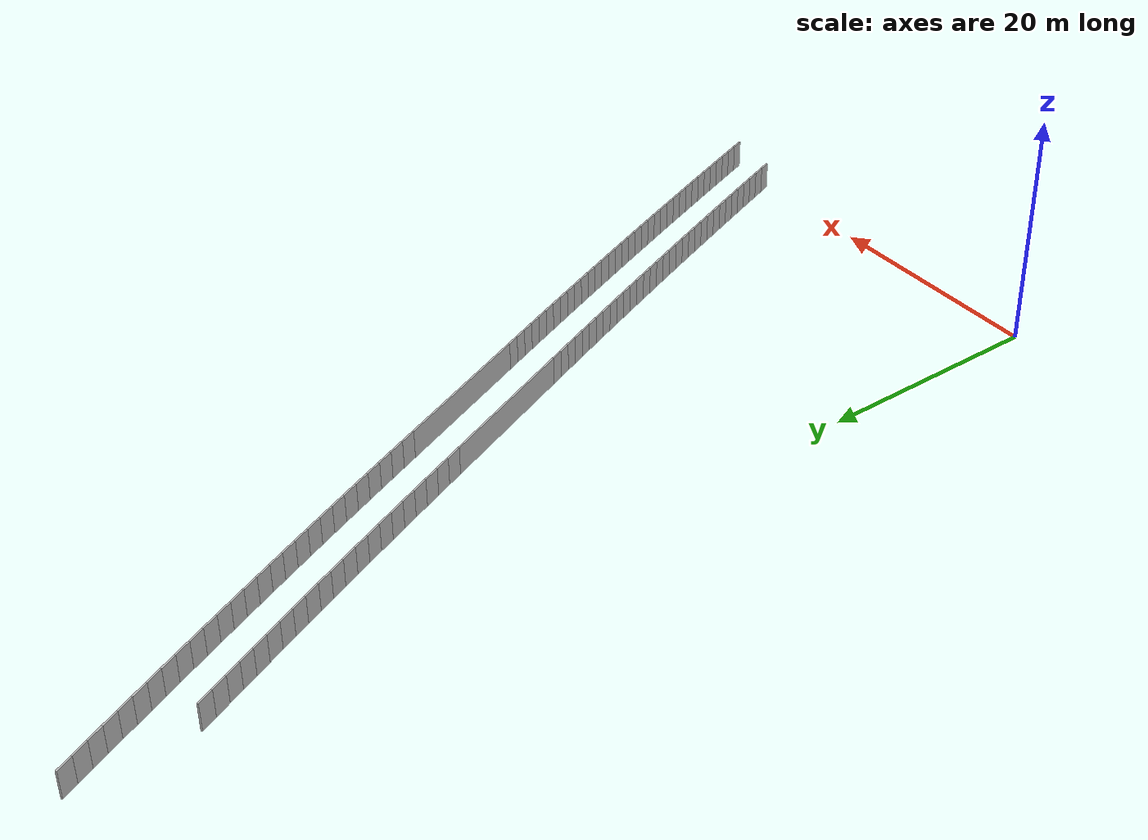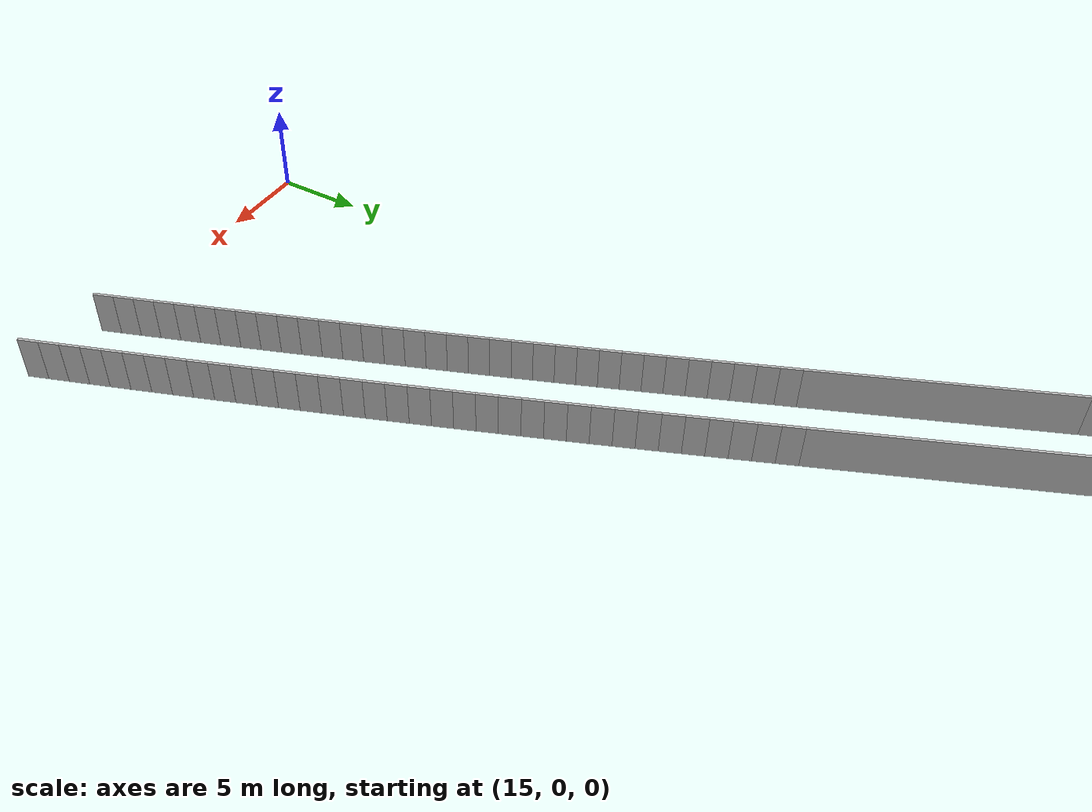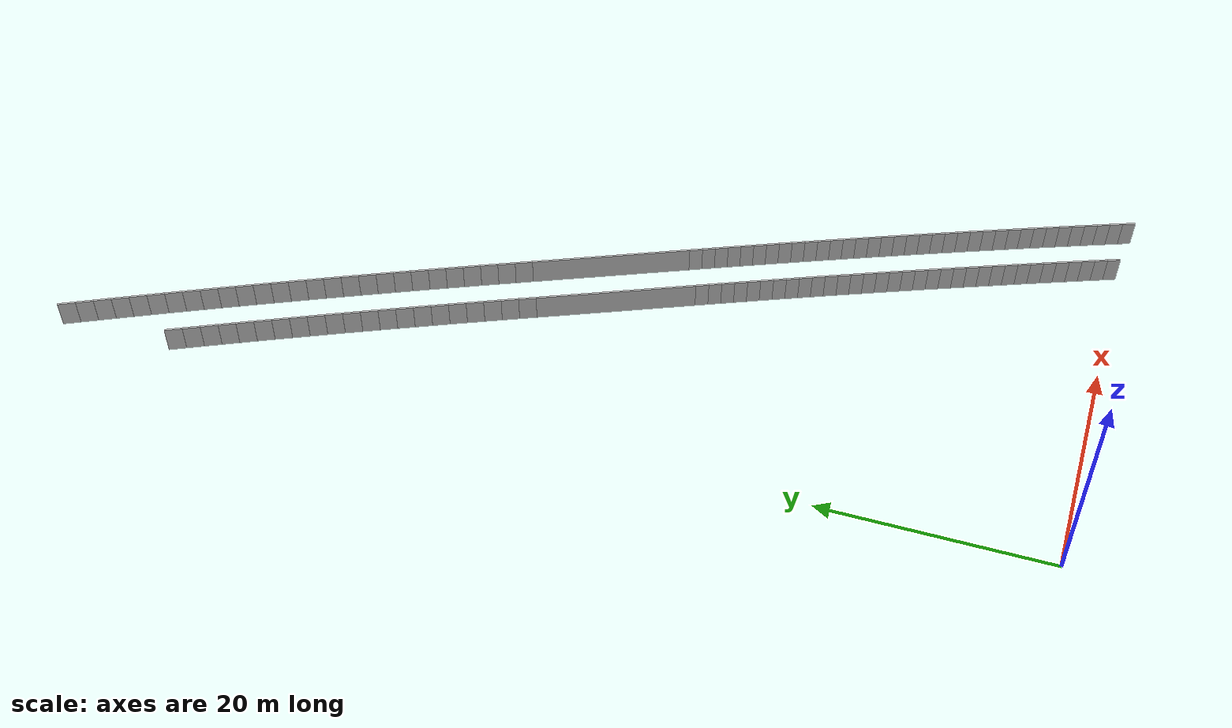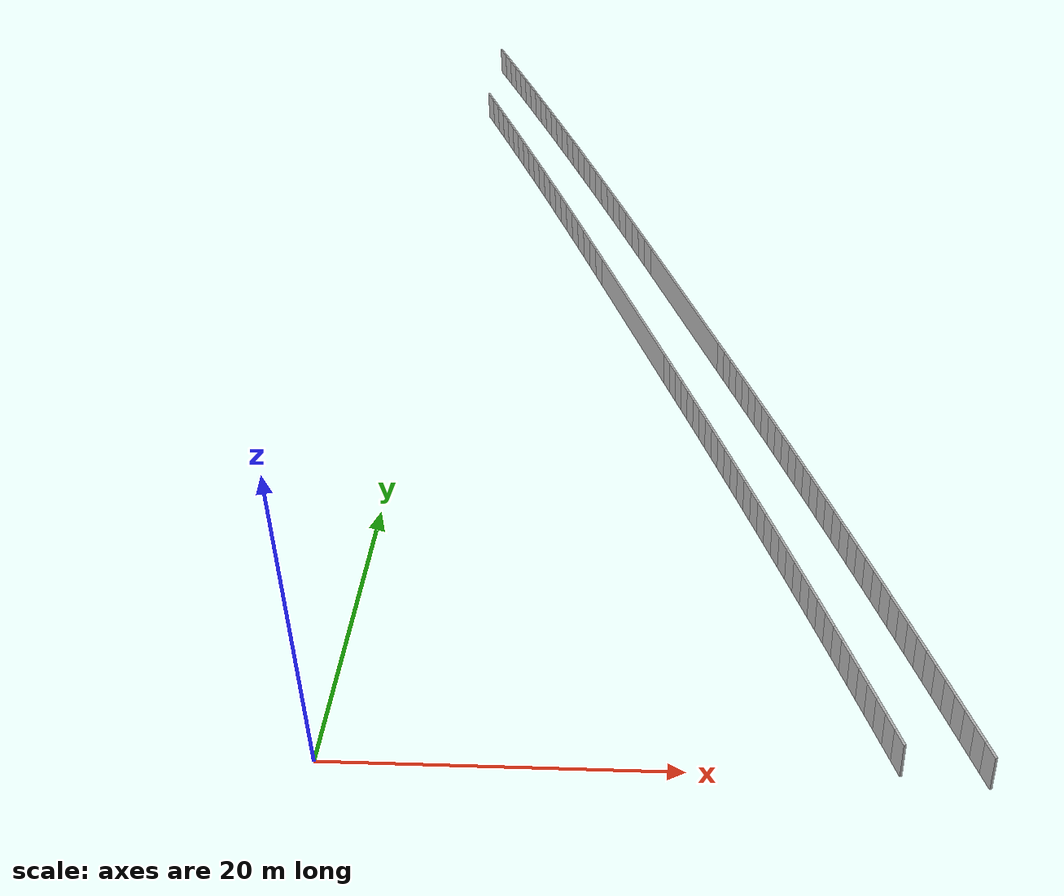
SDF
<?xml version="1.0" ?>
<sdf version="1.6">
  <model name="sps_2217">
    <pose frame="">0 0 0 0 -0 0</pose>
    <static>1</static>
    <self_collide>0</self_collide>
    <allow_auto_disable>0</allow_auto_disable>
    <link name="Wall73">
      <kinematic>0</kinematic>
      <gravity>1</gravity>
      <self_collide>0</self_collide>
      <collision name="collision">
        <geometry>
          <box>
            <size>13.7172 0.15 2.5</size>
          </box>
        </geometry>
        <pose frame="">0 0 0 0 -0 0</pose>
      </collision>
      <visual name="visual">
        <geometry>
          <box>
            <size>13.7172 0.15 2.5</size>
          </box>
        </geometry>
        <pose frame="">0 0 0 0 -0 0</pose>
        <cast_shadows>1</cast_shadows>
        <transparency>0.0</transparency>
      </visual>
      <pose frame="">19.0528 42.5171 1.25 0 0 -1.17752</pose>
    </link>
    <link name="Wall477">
      <kinematic>0</kinematic>
      <gravity>1</gravity>
      <self_collide>0</self_collide>
      <collision name="collision">
        <geometry>
          <box>
            <size>13.7271 0.15 2.5</size>
          </box>
        </geometry>
        <pose frame="">0 0 0 0 -0 0</pose>
      </collision>
      <visual name="visual">
        <geometry>
          <box>
            <size>13.7271 0.15 2.5</size>
          </box>
        </geometry>
        <pose frame="">0 0 0 0 -0 0</pose>
        <cast_shadows>1</cast_shadows>
        <transparency>0.0</transparency>
      </visual>
      <pose frame="">15.2295 40.9299 1.25 0 -0 1.96413</pose>
    </link>
    <link name="Wall3510">
      <kinematic>0</kinematic>
      <gravity>1</gravity>
      <self_collide>0</self_collide>
      <collision name="collision">
        <geometry>
          <box>
            <size>1.12133 0.15 2.5</size>
          </box>
        </geometry>
        <pose frame="">0 0 0 0 -0 0</pose>
      </collision>
      <visual name="visual">
        <geometry>
          <box>
            <size>1.12133 0.15 2.5</size>
          </box>
        </geometry>
        <pose frame="">0 0 0 0 -0 0</pose>
        <cast_shadows>1</cast_shadows>
        <transparency>0.0</transparency>
      </visual>
      <pose frame="">31.2198 0.685195 1.25 0 -0 1.92679</pose>
    </link>
    <link name="Wall3511">
      <kinematic>0</kinematic>
      <gravity>1</gravity>
      <self_collide>0</self_collide>
      <collision name="collision">
        <geometry>
          <box>
            <size>1.12134 0.15 2.5</size>
          </box>
        </geometry>
        <pose frame="">0 0 0 0 -0 0</pose>
      </collision>
      <visual name="visual">
        <geometry>
          <box>
            <size>1.12134 0.15 2.5</size>
          </box>
        </geometry>
        <pose frame="">0 0 0 0 -0 0</pose>
        <cast_shadows>1</cast_shadows>
        <transparency>0.0</transparency>
      </visual>
      <pose frame="">30.8285 1.73601 1.25 0 -0 1.92789</pose>
    </link>
    <link name="Wall3512">
      <kinematic>0</kinematic>
      <gravity>1</gravity>
      <self_collide>0</self_collide>
      <collision name="collision">
        <geometry>
          <box>
            <size>1.12145 0.15 2.5</size>
          </box>
        </geometry>
        <pose frame="">0 0 0 0 -0 0</pose>
      </collision>
      <visual name="visual">
        <geometry>
          <box>
            <size>1.12145 0.15 2.5</size>
          </box>
        </geometry>
        <pose frame="">0 0 0 0 -0 0</pose>
        <cast_shadows>1</cast_shadows>
        <transparency>0.0</transparency>
      </visual>
      <pose frame="">30.4358 2.78639 1.25 0 -0 1.92925</pose>
    </link>
    <link name="Wall3513">
      <kinematic>0</kinematic>
      <gravity>1</gravity>
      <self_collide>0</self_collide>
      <collision name="collision">
        <geometry>
          <box>
            <size>1.12134 0.15 2.5</size>
          </box>
        </geometry>
        <pose frame="">0 0 0 0 -0 0</pose>
      </collision>
      <visual name="visual">
        <geometry>
          <box>
            <size>1.12134 0.15 2.5</size>
          </box>
        </geometry>
        <pose frame="">0 0 0 0 -0 0</pose>
        <cast_shadows>1</cast_shadows>
        <transparency>0.0</transparency>
      </visual>
      <pose frame="">30.0417 3.83629 1.25 0 -0 1.93039</pose>
    </link>
    <link name="Wall3514">
      <kinematic>0</kinematic>
      <gravity>1</gravity>
      <self_collide>0</self_collide>
      <collision name="collision">
        <geometry>
          <box>
            <size>1.12144 0.15 2.5</size>
          </box>
        </geometry>
        <pose frame="">0 0 0 0 -0 0</pose>
      </collision>
      <visual name="visual">
        <geometry>
          <box>
            <size>1.12144 0.15 2.5</size>
          </box>
        </geometry>
        <pose frame="">0 0 0 0 -0 0</pose>
        <cast_shadows>1</cast_shadows>
        <transparency>0.0</transparency>
      </visual>
      <pose frame="">29.6464 4.8857 1.25 0 -0 1.93169</pose>
    </link>
    <link name="Wall3515">
      <kinematic>0</kinematic>
      <gravity>1</gravity>
      <self_collide>0</self_collide>
      <collision name="collision">
        <geometry>
          <box>
            <size>1.1213 0.15 2.5</size>
          </box>
        </geometry>
        <pose frame="">0 0 0 0 -0 0</pose>
      </collision>
      <visual name="visual">
        <geometry>
          <box>
            <size>1.1213 0.15 2.5</size>
          </box>
        </geometry>
        <pose frame="">0 0 0 0 -0 0</pose>
        <cast_shadows>1</cast_shadows>
        <transparency>0.0</transparency>
      </visual>
      <pose frame="">29.2498 5.93458 1.25 0 -0 1.93291</pose>
    </link>
    <link name="Wall3516">
      <kinematic>0</kinematic>
      <gravity>1</gravity>
      <self_collide>0</self_collide>
      <collision name="collision">
        <geometry>
          <box>
            <size>1.1213 0.15 2.5</size>
          </box>
        </geometry>
        <pose frame="">0 0 0 0 -0 0</pose>
      </collision>
      <visual name="visual">
        <geometry>
          <box>
            <size>1.1213 0.15 2.5</size>
          </box>
        </geometry>
        <pose frame="">0 0 0 0 -0 0</pose>
        <cast_shadows>1</cast_shadows>
        <transparency>0.0</transparency>
      </visual>
      <pose frame="">28.8521 6.98299 1.25 0 -0 1.93384</pose>
    </link>
    <link name="Wall3517">
      <kinematic>0</kinematic>
      <gravity>1</gravity>
      <self_collide>0</self_collide>
      <collision name="collision">
        <geometry>
          <box>
            <size>1.12147 0.15 2.5</size>
          </box>
        </geometry>
        <pose frame="">0 0 0 0 -0 0</pose>
      </collision>
      <visual name="visual">
        <geometry>
          <box>
            <size>1.12147 0.15 2.5</size>
          </box>
        </geometry>
        <pose frame="">0 0 0 0 -0 0</pose>
        <cast_shadows>1</cast_shadows>
        <transparency>0.0</transparency>
      </visual>
      <pose frame="">28.4531 8.03099 1.25 0 -0 1.93529</pose>
    </link>
    <link name="Wall3518">
      <kinematic>0</kinematic>
      <gravity>1</gravity>
      <self_collide>0</self_collide>
      <collision name="collision">
        <geometry>
          <box>
            <size>1.1215 0.15 2.5</size>
          </box>
        </geometry>
        <pose frame="">0 0 0 0 -0 0</pose>
      </collision>
      <visual name="visual">
        <geometry>
          <box>
            <size>1.1215 0.15 2.5</size>
          </box>
        </geometry>
        <pose frame="">0 0 0 0 -0 0</pose>
        <cast_shadows>1</cast_shadows>
        <transparency>0.0</transparency>
      </visual>
      <pose frame="">28.0528 9.0786 1.25 0 -0 1.93627</pose>
    </link>
    <link name="Wall3519">
      <kinematic>0</kinematic>
      <gravity>1</gravity>
      <self_collide>0</self_collide>
      <collision name="collision">
        <geometry>
          <box>
            <size>1.12141 0.15 2.5</size>
          </box>
        </geometry>
        <pose frame="">0 0 0 0 -0 0</pose>
      </collision>
      <visual name="visual">
        <geometry>
          <box>
            <size>1.12141 0.15 2.5</size>
          </box>
        </geometry>
        <pose frame="">0 0 0 0 -0 0</pose>
        <cast_shadows>1</cast_shadows>
        <transparency>0.0</transparency>
      </visual>
      <pose frame="">27.6514 10.1257 1.25 0 -0 1.93759</pose>
    </link>
    <link name="Wall3520">
      <kinematic>0</kinematic>
      <gravity>1</gravity>
      <self_collide>0</self_collide>
      <collision name="collision">
        <geometry>
          <box>
            <size>1.12138 0.15 2.5</size>
          </box>
        </geometry>
        <pose frame="">0 0 0 0 -0 0</pose>
      </collision>
      <visual name="visual">
        <geometry>
          <box>
            <size>1.12138 0.15 2.5</size>
          </box>
        </geometry>
        <pose frame="">0 0 0 0 -0 0</pose>
        <cast_shadows>1</cast_shadows>
        <transparency>0.0</transparency>
      </visual>
      <pose frame="">27.2487 11.1723 1.25 0 -0 1.93859</pose>
    </link>
    <link name="Wall3521">
      <kinematic>0</kinematic>
      <gravity>1</gravity>
      <self_collide>0</self_collide>
      <collision name="collision">
        <geometry>
          <box>
            <size>1.12149 0.15 2.5</size>
          </box>
        </geometry>
        <pose frame="">0 0 0 0 -0 0</pose>
      </collision>
      <visual name="visual">
        <geometry>
          <box>
            <size>1.12149 0.15 2.5</size>
          </box>
        </geometry>
        <pose frame="">0 0 0 0 -0 0</pose>
        <cast_shadows>1</cast_shadows>
        <transparency>0.0</transparency>
      </visual>
      <pose frame="">26.8448 12.2185 1.25 0 -0 1.93989</pose>
    </link>
    <link name="Wall3522">
      <kinematic>0</kinematic>
      <gravity>1</gravity>
      <self_collide>0</self_collide>
      <collision name="collision">
        <geometry>
          <box>
            <size>1.12125 0.15 2.5</size>
          </box>
        </geometry>
        <pose frame="">0 0 0 0 -0 0</pose>
      </collision>
      <visual name="visual">
        <geometry>
          <box>
            <size>1.12125 0.15 2.5</size>
          </box>
        </geometry>
        <pose frame="">0 0 0 0 -0 0</pose>
        <cast_shadows>1</cast_shadows>
        <transparency>0.0</transparency>
      </visual>
      <pose frame="">26.4396 13.2641 1.25 0 -0 1.94114</pose>
    </link>
    <link name="Wall3523">
      <kinematic>0</kinematic>
      <gravity>1</gravity>
      <self_collide>0</self_collide>
      <collision name="collision">
        <geometry>
          <box>
            <size>1.12125 0.15 2.5</size>
          </box>
        </geometry>
        <pose frame="">0 0 0 0 -0 0</pose>
      </collision>
      <visual name="visual">
        <geometry>
          <box>
            <size>1.12125 0.15 2.5</size>
          </box>
        </geometry>
        <pose frame="">0 0 0 0 -0 0</pose>
        <cast_shadows>1</cast_shadows>
        <transparency>0.0</transparency>
      </visual>
      <pose frame="">26.033 14.309 1.25 0 -0 1.94266</pose>
    </link>
    <link name="Wall3524">
      <kinematic>0</kinematic>
      <gravity>1</gravity>
      <self_collide>0</self_collide>
      <collision name="collision">
        <geometry>
          <box>
            <size>1.12131 0.15 2.5</size>
          </box>
        </geometry>
        <pose frame="">0 0 0 0 -0 0</pose>
      </collision>
      <visual name="visual">
        <geometry>
          <box>
            <size>1.12131 0.15 2.5</size>
          </box>
        </geometry>
        <pose frame="">0 0 0 0 -0 0</pose>
        <cast_shadows>1</cast_shadows>
        <transparency>0.0</transparency>
      </visual>
      <pose frame="">25.6251 15.3535 1.25 0 -0 1.9434</pose>
    </link>
    <link name="Wall3525">
      <kinematic>0</kinematic>
      <gravity>1</gravity>
      <self_collide>0</self_collide>
      <collision name="collision">
        <geometry>
          <box>
            <size>1.12131 0.15 2.5</size>
          </box>
        </geometry>
        <pose frame="">0 0 0 0 -0 0</pose>
      </collision>
      <visual name="visual">
        <geometry>
          <box>
            <size>1.12131 0.15 2.5</size>
          </box>
        </geometry>
        <pose frame="">0 0 0 0 -0 0</pose>
        <cast_shadows>1</cast_shadows>
        <transparency>0.0</transparency>
      </visual>
      <pose frame="">25.2162 16.3976 1.25 0 -0 1.94474</pose>
    </link>
    <link name="Wall3526">
      <kinematic>0</kinematic>
      <gravity>1</gravity>
      <self_collide>0</self_collide>
      <collision name="collision">
        <geometry>
          <box>
            <size>1.12134 0.15 2.5</size>
          </box>
        </geometry>
        <pose frame="">0 0 0 0 -0 0</pose>
      </collision>
      <visual name="visual">
        <geometry>
          <box>
            <size>1.12134 0.15 2.5</size>
          </box>
        </geometry>
        <pose frame="">0 0 0 0 -0 0</pose>
        <cast_shadows>1</cast_shadows>
        <transparency>0.0</transparency>
      </visual>
      <pose frame="">24.8061 17.4412 1.25 0 -0 1.94584</pose>
    </link>
    <link name="Wall3527">
      <kinematic>0</kinematic>
      <gravity>1</gravity>
      <self_collide>0</self_collide>
      <collision name="collision">
        <geometry>
          <box>
            <size>1.12122 0.15 2.5</size>
          </box>
        </geometry>
        <pose frame="">0 0 0 0 -0 0</pose>
      </collision>
      <visual name="visual">
        <geometry>
          <box>
            <size>1.12122 0.15 2.5</size>
          </box>
        </geometry>
        <pose frame="">0 0 0 0 -0 0</pose>
        <cast_shadows>1</cast_shadows>
        <transparency>0.0</transparency>
      </visual>
      <pose frame="">24.3947 18.4843 1.25 0 -0 1.94706</pose>
    </link>
    <link name="Wall3528">
      <kinematic>0</kinematic>
      <gravity>1</gravity>
      <self_collide>0</self_collide>
      <collision name="collision">
        <geometry>
          <box>
            <size>1.12159 0.15 2.5</size>
          </box>
        </geometry>
        <pose frame="">0 0 0 0 -0 0</pose>
      </collision>
      <visual name="visual">
        <geometry>
          <box>
            <size>1.12159 0.15 2.5</size>
          </box>
        </geometry>
        <pose frame="">0 0 0 0 -0 0</pose>
        <cast_shadows>1</cast_shadows>
        <transparency>0.0</transparency>
      </visual>
      <pose frame="">23.982 19.527 1.25 0 -0 1.94833</pose>
    </link>
    <link name="Wall3529">
      <kinematic>0</kinematic>
      <gravity>1</gravity>
      <self_collide>0</self_collide>
      <collision name="collision">
        <geometry>
          <box>
            <size>1.12136 0.15 2.5</size>
          </box>
        </geometry>
        <pose frame="">0 0 0 0 -0 0</pose>
      </collision>
      <visual name="visual">
        <geometry>
          <box>
            <size>1.12136 0.15 2.5</size>
          </box>
        </geometry>
        <pose frame="">0 0 0 0 -0 0</pose>
        <cast_shadows>1</cast_shadows>
        <transparency>0.0</transparency>
      </visual>
      <pose frame="">23.568 20.5693 1.25 0 -0 1.94929</pose>
    </link>
    <link name="Wall3530">
      <kinematic>0</kinematic>
      <gravity>1</gravity>
      <self_collide>0</self_collide>
      <collision name="collision">
        <geometry>
          <box>
            <size>1.12134 0.15 2.5</size>
          </box>
        </geometry>
        <pose frame="">0 0 0 0 -0 0</pose>
      </collision>
      <visual name="visual">
        <geometry>
          <box>
            <size>1.12134 0.15 2.5</size>
          </box>
        </geometry>
        <pose frame="">0 0 0 0 -0 0</pose>
        <cast_shadows>1</cast_shadows>
        <transparency>0.0</transparency>
      </visual>
      <pose frame="">23.1529 21.611 1.25 0 -0 1.95071</pose>
    </link>
    <link name="Wall3531">
      <kinematic>0</kinematic>
      <gravity>1</gravity>
      <self_collide>0</self_collide>
      <collision name="collision">
        <geometry>
          <box>
            <size>1.1216 0.15 2.5</size>
          </box>
        </geometry>
        <pose frame="">0 0 0 0 -0 0</pose>
      </collision>
      <visual name="visual">
        <geometry>
          <box>
            <size>1.1216 0.15 2.5</size>
          </box>
        </geometry>
        <pose frame="">0 0 0 0 -0 0</pose>
        <cast_shadows>1</cast_shadows>
        <transparency>0.0</transparency>
      </visual>
      <pose frame="">22.7365 22.6523 1.25 0 -0 1.95173</pose>
    </link>
    <link name="Wall3532">
      <kinematic>0</kinematic>
      <gravity>1</gravity>
      <self_collide>0</self_collide>
      <collision name="collision">
        <geometry>
          <box>
            <size>1.12129 0.15 2.5</size>
          </box>
        </geometry>
        <pose frame="">0 0 0 0 -0 0</pose>
      </collision>
      <visual name="visual">
        <geometry>
          <box>
            <size>1.12129 0.15 2.5</size>
          </box>
        </geometry>
        <pose frame="">0 0 0 0 -0 0</pose>
        <cast_shadows>1</cast_shadows>
        <transparency>0.0</transparency>
      </visual>
      <pose frame="">22.319 23.6931 1.25 0 -0 1.95295</pose>
    </link>
    <link name="Wall3533">
      <kinematic>0</kinematic>
      <gravity>1</gravity>
      <self_collide>0</self_collide>
      <collision name="collision">
        <geometry>
          <box>
            <size>1.12143 0.15 2.5</size>
          </box>
        </geometry>
        <pose frame="">0 0 0 0 -0 0</pose>
      </collision>
      <visual name="visual">
        <geometry>
          <box>
            <size>1.12143 0.15 2.5</size>
          </box>
        </geometry>
        <pose frame="">0 0 0 0 -0 0</pose>
        <cast_shadows>1</cast_shadows>
        <transparency>0.0</transparency>
      </visual>
      <pose frame="">21.9002 24.7333 1.25 0 -0 1.95413</pose>
    </link>
    <link name="Wall3534">
      <kinematic>0</kinematic>
      <gravity>1</gravity>
      <self_collide>0</self_collide>
      <collision name="collision">
        <geometry>
          <box>
            <size>1.12124 0.15 2.5</size>
          </box>
        </geometry>
        <pose frame="">0 0 0 0 -0 0</pose>
      </collision>
      <visual name="visual">
        <geometry>
          <box>
            <size>1.12124 0.15 2.5</size>
          </box>
        </geometry>
        <pose frame="">0 0 0 0 -0 0</pose>
        <cast_shadows>1</cast_shadows>
        <transparency>0.0</transparency>
      </visual>
      <pose frame="">21.4802 25.773 1.25 0 -0 1.95532</pose>
    </link>
    <link name="Wall3535">
      <kinematic>0</kinematic>
      <gravity>1</gravity>
      <self_collide>0</self_collide>
      <collision name="collision">
        <geometry>
          <box>
            <size>1.12143 0.15 2.5</size>
          </box>
        </geometry>
        <pose frame="">0 0 0 0 -0 0</pose>
      </collision>
      <visual name="visual">
        <geometry>
          <box>
            <size>1.12143 0.15 2.5</size>
          </box>
        </geometry>
        <pose frame="">0 0 0 0 -0 0</pose>
        <cast_shadows>1</cast_shadows>
        <transparency>0.0</transparency>
      </visual>
      <pose frame="">21.0589 26.8122 1.25 0 -0 1.9566</pose>
    </link>
    <link name="Wall3536">
      <kinematic>0</kinematic>
      <gravity>1</gravity>
      <self_collide>0</self_collide>
      <collision name="collision">
        <geometry>
          <box>
            <size>1.12132 0.15 2.5</size>
          </box>
        </geometry>
        <pose frame="">0 0 0 0 -0 0</pose>
      </collision>
      <visual name="visual">
        <geometry>
          <box>
            <size>1.12132 0.15 2.5</size>
          </box>
        </geometry>
        <pose frame="">0 0 0 0 -0 0</pose>
        <cast_shadows>1</cast_shadows>
        <transparency>0.0</transparency>
      </visual>
      <pose frame="">20.6363 27.8509 1.25 0 -0 1.95781</pose>
    </link>
    <link name="Wall3537">
      <kinematic>0</kinematic>
      <gravity>1</gravity>
      <self_collide>0</self_collide>
      <collision name="collision">
        <geometry>
          <box>
            <size>1.12142 0.15 2.5</size>
          </box>
        </geometry>
        <pose frame="">0 0 0 0 -0 0</pose>
      </collision>
      <visual name="visual">
        <geometry>
          <box>
            <size>1.12142 0.15 2.5</size>
          </box>
        </geometry>
        <pose frame="">0 0 0 0 -0 0</pose>
        <cast_shadows>1</cast_shadows>
        <transparency>0.0</transparency>
      </visual>
      <pose frame="">20.2125 28.8891 1.25 0 -0 1.95889</pose>
    </link>
    <link name="Wall3538">
      <kinematic>0</kinematic>
      <gravity>1</gravity>
      <self_collide>0</self_collide>
      <collision name="collision">
        <geometry>
          <box>
            <size>1.12149 0.15 2.5</size>
          </box>
        </geometry>
        <pose frame="">0 0 0 0 -0 0</pose>
      </collision>
      <visual name="visual">
        <geometry>
          <box>
            <size>1.12149 0.15 2.5</size>
          </box>
        </geometry>
        <pose frame="">0 0 0 0 -0 0</pose>
        <cast_shadows>1</cast_shadows>
        <transparency>0.0</transparency>
      </visual>
      <pose frame="">19.7875 29.9269 1.25 0 -0 1.96004</pose>
    </link>
    <link name="Wall3539">
      <kinematic>0</kinematic>
      <gravity>1</gravity>
      <self_collide>0</self_collide>
      <collision name="collision">
        <geometry>
          <box>
            <size>1.12139 0.15 2.5</size>
          </box>
        </geometry>
        <pose frame="">0 0 0 0 -0 0</pose>
      </collision>
      <visual name="visual">
        <geometry>
          <box>
            <size>1.12139 0.15 2.5</size>
          </box>
        </geometry>
        <pose frame="">0 0 0 0 -0 0</pose>
        <cast_shadows>1</cast_shadows>
        <transparency>0.0</transparency>
      </visual>
      <pose frame="">19.3613 30.9642 1.25 0 -0 1.96126</pose>
    </link>
    <link name="Wall3540">
      <kinematic>0</kinematic>
      <gravity>1</gravity>
      <self_collide>0</self_collide>
      <collision name="collision">
        <geometry>
          <box>
            <size>1.12132 0.15 2.5</size>
          </box>
        </geometry>
        <pose frame="">0 0 0 0 -0 0</pose>
      </collision>
      <visual name="visual">
        <geometry>
          <box>
            <size>1.12132 0.15 2.5</size>
          </box>
        </geometry>
        <pose frame="">0 0 0 0 -0 0</pose>
        <cast_shadows>1</cast_shadows>
        <transparency>0.0</transparency>
      </visual>
      <pose frame="">18.9339 32.0009 1.25 0 -0 1.9624</pose>
    </link>
    <link name="Wall3541">
      <kinematic>0</kinematic>
      <gravity>1</gravity>
      <self_collide>0</self_collide>
      <collision name="collision">
        <geometry>
          <box>
            <size>1.12134 0.15 2.5</size>
          </box>
        </geometry>
        <pose frame="">0 0 0 0 -0 0</pose>
      </collision>
      <visual name="visual">
        <geometry>
          <box>
            <size>1.12134 0.15 2.5</size>
          </box>
        </geometry>
        <pose frame="">0 0 0 0 -0 0</pose>
        <cast_shadows>1</cast_shadows>
        <transparency>0.0</transparency>
      </visual>
      <pose frame="">18.5053 33.0371 1.25 0 -0 1.96357</pose>
    </link>
    <link name="Wall3542">
      <kinematic>0</kinematic>
      <gravity>1</gravity>
      <self_collide>0</self_collide>
      <collision name="collision">
        <geometry>
          <box>
            <size>1.12137 0.15 2.5</size>
          </box>
        </geometry>
        <pose frame="">0 0 0 0 -0 0</pose>
      </collision>
      <visual name="visual">
        <geometry>
          <box>
            <size>1.12137 0.15 2.5</size>
          </box>
        </geometry>
        <pose frame="">0 0 0 0 -0 0</pose>
        <cast_shadows>1</cast_shadows>
        <transparency>0.0</transparency>
      </visual>
      <pose frame="">18.0754 34.0728 1.25 0 -0 1.96492</pose>
    </link>
    <link name="Wall6442">
      <kinematic>0</kinematic>
      <gravity>1</gravity>
      <self_collide>0</self_collide>
      <collision name="collision">
        <geometry>
          <box>
            <size>1.12616 0.15 2.5</size>
          </box>
        </geometry>
        <pose frame="">0 0 0 0 -0 0</pose>
      </collision>
      <visual name="visual">
        <geometry>
          <box>
            <size>1.12616 0.15 2.5</size>
          </box>
        </geometry>
        <pose frame="">0 0 0 0 -0 0</pose>
        <cast_shadows>1</cast_shadows>
        <transparency>0.0</transparency>
      </visual>
      <pose frame="">35.8824 0.0160665 1.25 0 -0 1.92462</pose>
    </link>
    <link name="Wall6443">
      <kinematic>0</kinematic>
      <gravity>1</gravity>
      <self_collide>0</self_collide>
      <collision name="collision">
        <geometry>
          <box>
            <size>1.12641 0.15 2.5</size>
          </box>
        </geometry>
        <pose frame="">0 0 0 0 -0 0</pose>
      </collision>
      <visual name="visual">
        <geometry>
          <box>
            <size>1.12641 0.15 2.5</size>
          </box>
        </geometry>
        <pose frame="">0 0 0 0 -0 0</pose>
        <cast_shadows>1</cast_shadows>
        <transparency>0.0</transparency>
      </visual>
      <pose frame="">35.4916 1.07237 1.25 0 -0 1.92569</pose>
    </link>
    <link name="Wall6444">
      <kinematic>0</kinematic>
      <gravity>1</gravity>
      <self_collide>0</self_collide>
      <collision name="collision">
        <geometry>
          <box>
            <size>1.12624 0.15 2.5</size>
          </box>
        </geometry>
        <pose frame="">0 0 0 0 -0 0</pose>
      </collision>
      <visual name="visual">
        <geometry>
          <box>
            <size>1.12624 0.15 2.5</size>
          </box>
        </geometry>
        <pose frame="">0 0 0 0 -0 0</pose>
        <cast_shadows>1</cast_shadows>
        <transparency>0.0</transparency>
      </visual>
      <pose frame="">35.0996 2.12828 1.25 0 -0 1.92685</pose>
    </link>
    <link name="Wall6445">
      <kinematic>0</kinematic>
      <gravity>1</gravity>
      <self_collide>0</self_collide>
      <collision name="collision">
        <geometry>
          <box>
            <size>1.12649 0.15 2.5</size>
          </box>
        </geometry>
        <pose frame="">0 0 0 0 -0 0</pose>
      </collision>
      <visual name="visual">
        <geometry>
          <box>
            <size>1.12649 0.15 2.5</size>
          </box>
        </geometry>
        <pose frame="">0 0 0 0 -0 0</pose>
        <cast_shadows>1</cast_shadows>
        <transparency>0.0</transparency>
      </visual>
      <pose frame="">34.7064 3.18379 1.25 0 -0 1.92792</pose>
    </link>
    <link name="Wall6446">
      <kinematic>0</kinematic>
      <gravity>1</gravity>
      <self_collide>0</self_collide>
      <collision name="collision">
        <geometry>
          <box>
            <size>1.12619 0.15 2.5</size>
          </box>
        </geometry>
        <pose frame="">0 0 0 0 -0 0</pose>
      </collision>
      <visual name="visual">
        <geometry>
          <box>
            <size>1.12619 0.15 2.5</size>
          </box>
        </geometry>
        <pose frame="">0 0 0 0 -0 0</pose>
        <cast_shadows>1</cast_shadows>
        <transparency>0.0</transparency>
      </visual>
      <pose frame="">34.3119 4.23878 1.25 0 -0 1.92935</pose>
    </link>
    <link name="Wall6447">
      <kinematic>0</kinematic>
      <gravity>1</gravity>
      <self_collide>0</self_collide>
      <collision name="collision">
        <geometry>
          <box>
            <size>1.12621 0.15 2.5</size>
          </box>
        </geometry>
        <pose frame="">0 0 0 0 -0 0</pose>
      </collision>
      <visual name="visual">
        <geometry>
          <box>
            <size>1.12621 0.15 2.5</size>
          </box>
        </geometry>
        <pose frame="">0 0 0 0 -0 0</pose>
        <cast_shadows>1</cast_shadows>
        <transparency>0.0</transparency>
      </visual>
      <pose frame="">33.9162 5.29317 1.25 0 -0 1.93033</pose>
    </link>
    <link name="Wall6448">
      <kinematic>0</kinematic>
      <gravity>1</gravity>
      <self_collide>0</self_collide>
      <collision name="collision">
        <geometry>
          <box>
            <size>1.12634 0.15 2.5</size>
          </box>
        </geometry>
        <pose frame="">0 0 0 0 -0 0</pose>
      </collision>
      <visual name="visual">
        <geometry>
          <box>
            <size>1.12634 0.15 2.5</size>
          </box>
        </geometry>
        <pose frame="">0 0 0 0 -0 0</pose>
        <cast_shadows>1</cast_shadows>
        <transparency>0.0</transparency>
      </visual>
      <pose frame="">33.5192 6.34718 1.25 0 -0 1.93156</pose>
    </link>
    <link name="Wall6449">
      <kinematic>0</kinematic>
      <gravity>1</gravity>
      <self_collide>0</self_collide>
      <collision name="collision">
        <geometry>
          <box>
            <size>1.1262 0.15 2.5</size>
          </box>
        </geometry>
        <pose frame="">0 0 0 0 -0 0</pose>
      </collision>
      <visual name="visual">
        <geometry>
          <box>
            <size>1.1262 0.15 2.5</size>
          </box>
        </geometry>
        <pose frame="">0 0 0 0 -0 0</pose>
        <cast_shadows>1</cast_shadows>
        <transparency>0.0</transparency>
      </visual>
      <pose frame="">33.1211 7.40071 1.25 0 -0 1.93276</pose>
    </link>
    <link name="Wall6450">
      <kinematic>0</kinematic>
      <gravity>1</gravity>
      <self_collide>0</self_collide>
      <collision name="collision">
        <geometry>
          <box>
            <size>1.12647 0.15 2.5</size>
          </box>
        </geometry>
        <pose frame="">0 0 0 0 -0 0</pose>
      </collision>
      <visual name="visual">
        <geometry>
          <box>
            <size>1.12647 0.15 2.5</size>
          </box>
        </geometry>
        <pose frame="">0 0 0 0 -0 0</pose>
        <cast_shadows>1</cast_shadows>
        <transparency>0.0</transparency>
      </visual>
      <pose frame="">32.7215 8.45381 1.25 0 -0 1.93401</pose>
    </link>
    <link name="Wall6451">
      <kinematic>0</kinematic>
      <gravity>1</gravity>
      <self_collide>0</self_collide>
      <collision name="collision">
        <geometry>
          <box>
            <size>1.12631 0.15 2.5</size>
          </box>
        </geometry>
        <pose frame="">0 0 0 0 -0 0</pose>
      </collision>
      <visual name="visual">
        <geometry>
          <box>
            <size>1.12631 0.15 2.5</size>
          </box>
        </geometry>
        <pose frame="">0 0 0 0 -0 0</pose>
        <cast_shadows>1</cast_shadows>
        <transparency>0.0</transparency>
      </visual>
      <pose frame="">32.3208 9.50648 1.25 0 -0 1.93516</pose>
    </link>
    <link name="Wall6452">
      <kinematic>0</kinematic>
      <gravity>1</gravity>
      <self_collide>0</self_collide>
      <collision name="collision">
        <geometry>
          <box>
            <size>1.12643 0.15 2.5</size>
          </box>
        </geometry>
        <pose frame="">0 0 0 0 -0 0</pose>
      </collision>
      <visual name="visual">
        <geometry>
          <box>
            <size>1.12643 0.15 2.5</size>
          </box>
        </geometry>
        <pose frame="">0 0 0 0 -0 0</pose>
        <cast_shadows>1</cast_shadows>
        <transparency>0.0</transparency>
      </visual>
      <pose frame="">31.9188 10.5587 1.25 0 -0 1.93634</pose>
    </link>
    <link name="Wall6453">
      <kinematic>0</kinematic>
      <gravity>1</gravity>
      <self_collide>0</self_collide>
      <collision name="collision">
        <geometry>
          <box>
            <size>1.12617 0.15 2.5</size>
          </box>
        </geometry>
        <pose frame="">0 0 0 0 -0 0</pose>
      </collision>
      <visual name="visual">
        <geometry>
          <box>
            <size>1.12617 0.15 2.5</size>
          </box>
        </geometry>
        <pose frame="">0 0 0 0 -0 0</pose>
        <cast_shadows>1</cast_shadows>
        <transparency>0.0</transparency>
      </visual>
      <pose frame="">31.5154 11.6103 1.25 0 -0 1.93771</pose>
    </link>
    <link name="Wall6454">
      <kinematic>0</kinematic>
      <gravity>1</gravity>
      <self_collide>0</self_collide>
      <collision name="collision">
        <geometry>
          <box>
            <size>1.12635 0.15 2.5</size>
          </box>
        </geometry>
        <pose frame="">0 0 0 0 -0 0</pose>
      </collision>
      <visual name="visual">
        <geometry>
          <box>
            <size>1.12635 0.15 2.5</size>
          </box>
        </geometry>
        <pose frame="">0 0 0 0 -0 0</pose>
        <cast_shadows>1</cast_shadows>
        <transparency>0.0</transparency>
      </visual>
      <pose frame="">31.111 12.6614 1.25 0 -0 1.93857</pose>
    </link>
    <link name="Wall6455">
      <kinematic>0</kinematic>
      <gravity>1</gravity>
      <self_collide>0</self_collide>
      <collision name="collision">
        <geometry>
          <box>
            <size>1.1263 0.15 2.5</size>
          </box>
        </geometry>
        <pose frame="">0 0 0 0 -0 0</pose>
      </collision>
      <visual name="visual">
        <geometry>
          <box>
            <size>1.1263 0.15 2.5</size>
          </box>
        </geometry>
        <pose frame="">0 0 0 0 -0 0</pose>
        <cast_shadows>1</cast_shadows>
        <transparency>0.0</transparency>
      </visual>
      <pose frame="">30.7053 13.7121 1.25 0 -0 1.93998</pose>
    </link>
    <link name="Wall6456">
      <kinematic>0</kinematic>
      <gravity>1</gravity>
      <self_collide>0</self_collide>
      <collision name="collision">
        <geometry>
          <box>
            <size>1.12599 0.15 2.5</size>
          </box>
        </geometry>
        <pose frame="">0 0 0 0 -0 0</pose>
      </collision>
      <visual name="visual">
        <geometry>
          <box>
            <size>1.12599 0.15 2.5</size>
          </box>
        </geometry>
        <pose frame="">0 0 0 0 -0 0</pose>
        <cast_shadows>1</cast_shadows>
        <transparency>0.0</transparency>
      </visual>
      <pose frame="">30.2981 14.7621 1.25 0 -0 1.94137</pose>
    </link>
    <link name="Wall6457">
      <kinematic>0</kinematic>
      <gravity>1</gravity>
      <self_collide>0</self_collide>
      <collision name="collision">
        <geometry>
          <box>
            <size>1.12625 0.15 2.5</size>
          </box>
        </geometry>
        <pose frame="">0 0 0 0 -0 0</pose>
      </collision>
      <visual name="visual">
        <geometry>
          <box>
            <size>1.12625 0.15 2.5</size>
          </box>
        </geometry>
        <pose frame="">0 0 0 0 -0 0</pose>
        <cast_shadows>1</cast_shadows>
        <transparency>0.0</transparency>
      </visual>
      <pose frame="">29.8899 15.8116 1.25 0 -0 1.94227</pose>
    </link>
    <link name="Wall6458">
      <kinematic>0</kinematic>
      <gravity>1</gravity>
      <self_collide>0</self_collide>
      <collision name="collision">
        <geometry>
          <box>
            <size>1.12631 0.15 2.5</size>
          </box>
        </geometry>
        <pose frame="">0 0 0 0 -0 0</pose>
      </collision>
      <visual name="visual">
        <geometry>
          <box>
            <size>1.12631 0.15 2.5</size>
          </box>
        </geometry>
        <pose frame="">0 0 0 0 -0 0</pose>
        <cast_shadows>1</cast_shadows>
        <transparency>0.0</transparency>
      </visual>
      <pose frame="">29.4803 16.8608 1.25 0 -0 1.94358</pose>
    </link>
    <link name="Wall6459">
      <kinematic>0</kinematic>
      <gravity>1</gravity>
      <self_collide>0</self_collide>
      <collision name="collision">
        <geometry>
          <box>
            <size>1.12615 0.15 2.5</size>
          </box>
        </geometry>
        <pose frame="">0 0 0 0 -0 0</pose>
      </collision>
      <visual name="visual">
        <geometry>
          <box>
            <size>1.12615 0.15 2.5</size>
          </box>
        </geometry>
        <pose frame="">0 0 0 0 -0 0</pose>
        <cast_shadows>1</cast_shadows>
        <transparency>0.0</transparency>
      </visual>
      <pose frame="">29.0696 17.9095 1.25 0 -0 1.94457</pose>
    </link>
    <link name="Wall6460">
      <kinematic>0</kinematic>
      <gravity>1</gravity>
      <self_collide>0</self_collide>
      <collision name="collision">
        <geometry>
          <box>
            <size>1.12633 0.15 2.5</size>
          </box>
        </geometry>
        <pose frame="">0 0 0 0 -0 0</pose>
      </collision>
      <visual name="visual">
        <geometry>
          <box>
            <size>1.12633 0.15 2.5</size>
          </box>
        </geometry>
        <pose frame="">0 0 0 0 -0 0</pose>
        <cast_shadows>1</cast_shadows>
        <transparency>0.0</transparency>
      </visual>
      <pose frame="">28.6577 18.9577 1.25 0 -0 1.94585</pose>
    </link>
    <link name="Wall6461">
      <kinematic>0</kinematic>
      <gravity>1</gravity>
      <self_collide>0</self_collide>
      <collision name="collision">
        <geometry>
          <box>
            <size>1.12645 0.15 2.5</size>
          </box>
        </geometry>
        <pose frame="">0 0 0 0 -0 0</pose>
      </collision>
      <visual name="visual">
        <geometry>
          <box>
            <size>1.12645 0.15 2.5</size>
          </box>
        </geometry>
        <pose frame="">0 0 0 0 -0 0</pose>
        <cast_shadows>1</cast_shadows>
        <transparency>0.0</transparency>
      </visual>
      <pose frame="">28.2444 20.0055 1.25 0 -0 1.94715</pose>
    </link>
    <link name="Wall6462">
      <kinematic>0</kinematic>
      <gravity>1</gravity>
      <self_collide>0</self_collide>
      <collision name="collision">
        <geometry>
          <box>
            <size>1.12624 0.15 2.5</size>
          </box>
        </geometry>
        <pose frame="">0 0 0 0 -0 0</pose>
      </collision>
      <visual name="visual">
        <geometry>
          <box>
            <size>1.12624 0.15 2.5</size>
          </box>
        </geometry>
        <pose frame="">0 0 0 0 -0 0</pose>
        <cast_shadows>1</cast_shadows>
        <transparency>0.0</transparency>
      </visual>
      <pose frame="">27.8299 21.0528 1.25 0 -0 1.94815</pose>
    </link>
    <link name="Wall6463">
      <kinematic>0</kinematic>
      <gravity>1</gravity>
      <self_collide>0</self_collide>
      <collision name="collision">
        <geometry>
          <box>
            <size>1.12619 0.15 2.5</size>
          </box>
        </geometry>
        <pose frame="">0 0 0 0 -0 0</pose>
      </collision>
      <visual name="visual">
        <geometry>
          <box>
            <size>1.12619 0.15 2.5</size>
          </box>
        </geometry>
        <pose frame="">0 0 0 0 -0 0</pose>
        <cast_shadows>1</cast_shadows>
        <transparency>0.0</transparency>
      </visual>
      <pose frame="">27.4143 22.0995 1.25 0 -0 1.94951</pose>
    </link>
    <link name="Wall6464">
      <kinematic>0</kinematic>
      <gravity>1</gravity>
      <self_collide>0</self_collide>
      <collision name="collision">
        <geometry>
          <box>
            <size>1.1263 0.15 2.5</size>
          </box>
        </geometry>
        <pose frame="">0 0 0 0 -0 0</pose>
      </collision>
      <visual name="visual">
        <geometry>
          <box>
            <size>1.1263 0.15 2.5</size>
          </box>
        </geometry>
        <pose frame="">0 0 0 0 -0 0</pose>
        <cast_shadows>1</cast_shadows>
        <transparency>0.0</transparency>
      </visual>
      <pose frame="">26.9973 23.1457 1.25 0 -0 1.95064</pose>
    </link>
    <link name="Wall6465">
      <kinematic>0</kinematic>
      <gravity>1</gravity>
      <self_collide>0</self_collide>
      <collision name="collision">
        <geometry>
          <box>
            <size>1.12629 0.15 2.5</size>
          </box>
        </geometry>
        <pose frame="">0 0 0 0 -0 0</pose>
      </collision>
      <visual name="visual">
        <geometry>
          <box>
            <size>1.12629 0.15 2.5</size>
          </box>
        </geometry>
        <pose frame="">0 0 0 0 -0 0</pose>
        <cast_shadows>1</cast_shadows>
        <transparency>0.0</transparency>
      </visual>
      <pose frame="">26.5792 24.1915 1.25 0 -0 1.95163</pose>
    </link>
    <link name="Wall6466">
      <kinematic>0</kinematic>
      <gravity>1</gravity>
      <self_collide>0</self_collide>
      <collision name="collision">
        <geometry>
          <box>
            <size>1.12646 0.15 2.5</size>
          </box>
        </geometry>
        <pose frame="">0 0 0 0 -0 0</pose>
      </collision>
      <visual name="visual">
        <geometry>
          <box>
            <size>1.12646 0.15 2.5</size>
          </box>
        </geometry>
        <pose frame="">0 0 0 0 -0 0</pose>
        <cast_shadows>1</cast_shadows>
        <transparency>0.0</transparency>
      </visual>
      <pose frame="">26.1598 25.2369 1.25 0 -0 1.95303</pose>
    </link>
    <link name="Wall6467">
      <kinematic>0</kinematic>
      <gravity>1</gravity>
      <self_collide>0</self_collide>
      <collision name="collision">
        <geometry>
          <box>
            <size>1.12617 0.15 2.5</size>
          </box>
        </geometry>
        <pose frame="">0 0 0 0 -0 0</pose>
      </collision>
      <visual name="visual">
        <geometry>
          <box>
            <size>1.12617 0.15 2.5</size>
          </box>
        </geometry>
        <pose frame="">0 0 0 0 -0 0</pose>
        <cast_shadows>1</cast_shadows>
        <transparency>0.0</transparency>
      </visual>
      <pose frame="">25.7391 26.2817 1.25 0 -0 1.95413</pose>
    </link>
    <link name="Wall6468">
      <kinematic>0</kinematic>
      <gravity>1</gravity>
      <self_collide>0</self_collide>
      <collision name="collision">
        <geometry>
          <box>
            <size>1.1263 0.15 2.5</size>
          </box>
        </geometry>
        <pose frame="">0 0 0 0 -0 0</pose>
      </collision>
      <visual name="visual">
        <geometry>
          <box>
            <size>1.1263 0.15 2.5</size>
          </box>
        </geometry>
        <pose frame="">0 0 0 0 -0 0</pose>
        <cast_shadows>1</cast_shadows>
        <transparency>0.0</transparency>
      </visual>
      <pose frame="">25.3172 27.3259 1.25 0 -0 1.95543</pose>
    </link>
    <link name="Wall6469">
      <kinematic>0</kinematic>
      <gravity>1</gravity>
      <self_collide>0</self_collide>
      <collision name="collision">
        <geometry>
          <box>
            <size>1.12636 0.15 2.5</size>
          </box>
        </geometry>
        <pose frame="">0 0 0 0 -0 0</pose>
      </collision>
      <visual name="visual">
        <geometry>
          <box>
            <size>1.12636 0.15 2.5</size>
          </box>
        </geometry>
        <pose frame="">0 0 0 0 -0 0</pose>
        <cast_shadows>1</cast_shadows>
        <transparency>0.0</transparency>
      </visual>
      <pose frame="">24.8939 28.3697 1.25 0 -0 1.95658</pose>
    </link>
    <link name="Wall6470">
      <kinematic>0</kinematic>
      <gravity>1</gravity>
      <self_collide>0</self_collide>
      <collision name="collision">
        <geometry>
          <box>
            <size>1.12623 0.15 2.5</size>
          </box>
        </geometry>
        <pose frame="">0 0 0 0 -0 0</pose>
      </collision>
      <visual name="visual">
        <geometry>
          <box>
            <size>1.12623 0.15 2.5</size>
          </box>
        </geometry>
        <pose frame="">0 0 0 0 -0 0</pose>
        <cast_shadows>1</cast_shadows>
        <transparency>0.0</transparency>
      </visual>
      <pose frame="">24.4695 29.413 1.25 0 -0 1.95773</pose>
    </link>
    <link name="Wall6471">
      <kinematic>0</kinematic>
      <gravity>1</gravity>
      <self_collide>0</self_collide>
      <collision name="collision">
        <geometry>
          <box>
            <size>1.12635 0.15 2.5</size>
          </box>
        </geometry>
        <pose frame="">0 0 0 0 -0 0</pose>
      </collision>
      <visual name="visual">
        <geometry>
          <box>
            <size>1.12635 0.15 2.5</size>
          </box>
        </geometry>
        <pose frame="">0 0 0 0 -0 0</pose>
        <cast_shadows>1</cast_shadows>
        <transparency>0.0</transparency>
      </visual>
      <pose frame="">24.0439 30.4558 1.25 0 -0 1.95886</pose>
    </link>
    <link name="Wall6472">
      <kinematic>0</kinematic>
      <gravity>1</gravity>
      <self_collide>0</self_collide>
      <collision name="collision">
        <geometry>
          <box>
            <size>1.12635 0.15 2.5</size>
          </box>
        </geometry>
        <pose frame="">0 0 0 0 -0 0</pose>
      </collision>
      <visual name="visual">
        <geometry>
          <box>
            <size>1.12635 0.15 2.5</size>
          </box>
        </geometry>
        <pose frame="">0 0 0 0 -0 0</pose>
        <cast_shadows>1</cast_shadows>
        <transparency>0.0</transparency>
      </visual>
      <pose frame="">23.6171 31.4981 1.25 0 -0 1.96015</pose>
    </link>
    <link name="Wall6473">
      <kinematic>0</kinematic>
      <gravity>1</gravity>
      <self_collide>0</self_collide>
      <collision name="collision">
        <geometry>
          <box>
            <size>1.12639 0.15 2.5</size>
          </box>
        </geometry>
        <pose frame="">0 0 0 0 -0 0</pose>
      </collision>
      <visual name="visual">
        <geometry>
          <box>
            <size>1.12639 0.15 2.5</size>
          </box>
        </geometry>
        <pose frame="">0 0 0 0 -0 0</pose>
        <cast_shadows>1</cast_shadows>
        <transparency>0.0</transparency>
      </visual>
      <pose frame="">23.1889 32.5399 1.25 0 -0 1.96137</pose>
    </link>
    <link name="Wall6474">
      <kinematic>0</kinematic>
      <gravity>1</gravity>
      <self_collide>0</self_collide>
      <collision name="collision">
        <geometry>
          <box>
            <size>1.12625 0.15 2.5</size>
          </box>
        </geometry>
        <pose frame="">0 0 0 0 -0 0</pose>
      </collision>
      <visual name="visual">
        <geometry>
          <box>
            <size>1.12625 0.15 2.5</size>
          </box>
        </geometry>
        <pose frame="">0 0 0 0 -0 0</pose>
        <cast_shadows>1</cast_shadows>
        <transparency>0.0</transparency>
      </visual>
      <pose frame="">22.7595 33.5812 1.25 0 -0 1.96235</pose>
    </link>
    <link name="Wall6475">
      <kinematic>0</kinematic>
      <gravity>1</gravity>
      <self_collide>0</self_collide>
      <collision name="collision">
        <geometry>
          <box>
            <size>1.1264 0.15 2.5</size>
          </box>
        </geometry>
        <pose frame="">0 0 0 0 -0 0</pose>
      </collision>
      <visual name="visual">
        <geometry>
          <box>
            <size>1.1264 0.15 2.5</size>
          </box>
        </geometry>
        <pose frame="">0 0 0 0 -0 0</pose>
        <cast_shadows>1</cast_shadows>
        <transparency>0.0</transparency>
      </visual>
      <pose frame="">22.329 34.622 1.25 0 -0 1.96365</pose>
    </link>
    <link name="Wall6476">
      <kinematic>0</kinematic>
      <gravity>1</gravity>
      <self_collide>0</self_collide>
      <collision name="collision">
        <geometry>
          <box>
            <size>1.12611 0.15 2.5</size>
          </box>
        </geometry>
        <pose frame="">0 0 0 0 -0 0</pose>
      </collision>
      <visual name="visual">
        <geometry>
          <box>
            <size>1.12611 0.15 2.5</size>
          </box>
        </geometry>
        <pose frame="">0 0 0 0 -0 0</pose>
        <cast_shadows>1</cast_shadows>
        <transparency>0.0</transparency>
      </visual>
      <pose frame="">21.8972 35.6622 1.25 0 -0 1.96487</pose>
    </link>
    <link name="Wall10210">
      <kinematic>0</kinematic>
      <gravity>1</gravity>
      <self_collide>0</self_collide>
      <collision name="collision">
        <geometry>
          <box>
            <size>1.49624 0.15 2.5</size>
          </box>
        </geometry>
        <pose frame="">0 0 0 0 -0 0</pose>
      </collision>
      <visual name="visual">
        <geometry>
          <box>
            <size>1.49624 0.15 2.5</size>
          </box>
        </geometry>
        <pose frame="">0 0 0 0 -0 0</pose>
        <cast_shadows>1</cast_shadows>
        <transparency>0.0</transparency>
      </visual>
      <pose frame="">12.3122 47.9603 1.25 0 -0 1.96406</pose>
    </link>
    <link name="Wall10211">
      <kinematic>0</kinematic>
      <gravity>1</gravity>
      <self_collide>0</self_collide>
      <collision name="collision">
        <geometry>
          <box>
            <size>1.49641 0.15 2.5</size>
          </box>
        </geometry>
        <pose frame="">0 0 0 0 -0 0</pose>
      </collision>
      <visual name="visual">
        <geometry>
          <box>
            <size>1.49641 0.15 2.5</size>
          </box>
        </geometry>
        <pose frame="">0 0 0 0 -0 0</pose>
        <cast_shadows>1</cast_shadows>
        <transparency>0.0</transparency>
      </visual>
      <pose frame="">11.7378 49.342 1.25 0 -0 1.96551</pose>
    </link>
    <link name="Wall10212">
      <kinematic>0</kinematic>
      <gravity>1</gravity>
      <self_collide>0</self_collide>
      <collision name="collision">
        <geometry>
          <box>
            <size>1.49656 0.15 2.5</size>
          </box>
        </geometry>
        <pose frame="">0 0 0 0 -0 0</pose>
      </collision>
      <visual name="visual">
        <geometry>
          <box>
            <size>1.49656 0.15 2.5</size>
          </box>
        </geometry>
        <pose frame="">0 0 0 0 -0 0</pose>
        <cast_shadows>1</cast_shadows>
        <transparency>0.0</transparency>
      </visual>
      <pose frame="">11.1612 50.723 1.25 0 -0 1.96702</pose>
    </link>
    <link name="Wall10213">
      <kinematic>0</kinematic>
      <gravity>1</gravity>
      <self_collide>0</self_collide>
      <collision name="collision">
        <geometry>
          <box>
            <size>1.49668 0.15 2.5</size>
          </box>
        </geometry>
        <pose frame="">0 0 0 0 -0 0</pose>
      </collision>
      <visual name="visual">
        <geometry>
          <box>
            <size>1.49668 0.15 2.5</size>
          </box>
        </geometry>
        <pose frame="">0 0 0 0 -0 0</pose>
        <cast_shadows>1</cast_shadows>
        <transparency>0.0</transparency>
      </visual>
      <pose frame="">10.5826 52.1032 1.25 0 -0 1.96858</pose>
    </link>
    <link name="Wall10214">
      <kinematic>0</kinematic>
      <gravity>1</gravity>
      <self_collide>0</self_collide>
      <collision name="collision">
        <geometry>
          <box>
            <size>1.49653 0.15 2.5</size>
          </box>
        </geometry>
        <pose frame="">0 0 0 0 -0 0</pose>
      </collision>
      <visual name="visual">
        <geometry>
          <box>
            <size>1.49653 0.15 2.5</size>
          </box>
        </geometry>
        <pose frame="">0 0 0 0 -0 0</pose>
        <cast_shadows>1</cast_shadows>
        <transparency>0.0</transparency>
      </visual>
      <pose frame="">10.0018 53.4825 1.25 0 -0 1.97012</pose>
    </link>
    <link name="Wall10215">
      <kinematic>0</kinematic>
      <gravity>1</gravity>
      <self_collide>0</self_collide>
      <collision name="collision">
        <geometry>
          <box>
            <size>1.49653 0.15 2.5</size>
          </box>
        </geometry>
        <pose frame="">0 0 0 0 -0 0</pose>
      </collision>
      <visual name="visual">
        <geometry>
          <box>
            <size>1.49653 0.15 2.5</size>
          </box>
        </geometry>
        <pose frame="">0 0 0 0 -0 0</pose>
        <cast_shadows>1</cast_shadows>
        <transparency>0.0</transparency>
      </visual>
      <pose frame="">9.41875 54.8608 1.25 0 -0 1.97181</pose>
    </link>
    <link name="Wall10216">
      <kinematic>0</kinematic>
      <gravity>1</gravity>
      <self_collide>0</self_collide>
      <collision name="collision">
        <geometry>
          <box>
            <size>1.49639 0.15 2.5</size>
          </box>
        </geometry>
        <pose frame="">0 0 0 0 -0 0</pose>
      </collision>
      <visual name="visual">
        <geometry>
          <box>
            <size>1.49639 0.15 2.5</size>
          </box>
        </geometry>
        <pose frame="">0 0 0 0 -0 0</pose>
        <cast_shadows>1</cast_shadows>
        <transparency>0.0</transparency>
      </visual>
      <pose frame="">8.83355 56.2381 1.25 0 -0 1.97335</pose>
    </link>
    <link name="Wall10217">
      <kinematic>0</kinematic>
      <gravity>1</gravity>
      <self_collide>0</self_collide>
      <collision name="collision">
        <geometry>
          <box>
            <size>1.49662 0.15 2.5</size>
          </box>
        </geometry>
        <pose frame="">0 0 0 0 -0 0</pose>
      </collision>
      <visual name="visual">
        <geometry>
          <box>
            <size>1.49662 0.15 2.5</size>
          </box>
        </geometry>
        <pose frame="">0 0 0 0 -0 0</pose>
        <cast_shadows>1</cast_shadows>
        <transparency>0.0</transparency>
      </visual>
      <pose frame="">8.24615 57.6145 1.25 0 -0 1.97497</pose>
    </link>
    <link name="Wall10218">
      <kinematic>0</kinematic>
      <gravity>1</gravity>
      <self_collide>0</self_collide>
      <collision name="collision">
        <geometry>
          <box>
            <size>1.49649 0.15 2.5</size>
          </box>
        </geometry>
        <pose frame="">0 0 0 0 -0 0</pose>
      </collision>
      <visual name="visual">
        <geometry>
          <box>
            <size>1.49649 0.15 2.5</size>
          </box>
        </geometry>
        <pose frame="">0 0 0 0 -0 0</pose>
        <cast_shadows>1</cast_shadows>
        <transparency>0.0</transparency>
      </visual>
      <pose frame="">7.65655 58.99 1.25 0 -0 1.97652</pose>
    </link>
    <link name="Wall10219">
      <kinematic>0</kinematic>
      <gravity>1</gravity>
      <self_collide>0</self_collide>
      <collision name="collision">
        <geometry>
          <box>
            <size>1.49638 0.15 2.5</size>
          </box>
        </geometry>
        <pose frame="">0 0 0 0 -0 0</pose>
      </collision>
      <visual name="visual">
        <geometry>
          <box>
            <size>1.49638 0.15 2.5</size>
          </box>
        </geometry>
        <pose frame="">0 0 0 0 -0 0</pose>
        <cast_shadows>1</cast_shadows>
        <transparency>0.0</transparency>
      </visual>
      <pose frame="">7.06484 60.3645 1.25 0 -0 1.9781</pose>
    </link>
    <link name="Wall10220">
      <kinematic>0</kinematic>
      <gravity>1</gravity>
      <self_collide>0</self_collide>
      <collision name="collision">
        <geometry>
          <box>
            <size>1.49658 0.15 2.5</size>
          </box>
        </geometry>
        <pose frame="">0 0 0 0 -0 0</pose>
      </collision>
      <visual name="visual">
        <geometry>
          <box>
            <size>1.49658 0.15 2.5</size>
          </box>
        </geometry>
        <pose frame="">0 0 0 0 -0 0</pose>
        <cast_shadows>1</cast_shadows>
        <transparency>0.0</transparency>
      </visual>
      <pose frame="">6.47097 61.7381 1.25 0 -0 1.97965</pose>
    </link>
    <link name="Wall10221">
      <kinematic>0</kinematic>
      <gravity>1</gravity>
      <self_collide>0</self_collide>
      <collision name="collision">
        <geometry>
          <box>
            <size>1.49645 0.15 2.5</size>
          </box>
        </geometry>
        <pose frame="">0 0 0 0 -0 0</pose>
      </collision>
      <visual name="visual">
        <geometry>
          <box>
            <size>1.49645 0.15 2.5</size>
          </box>
        </geometry>
        <pose frame="">0 0 0 0 -0 0</pose>
        <cast_shadows>1</cast_shadows>
        <transparency>0.0</transparency>
      </visual>
      <pose frame="">5.87496 63.1108 1.25 0 -0 1.98119</pose>
    </link>
    <link name="Wall10222">
      <kinematic>0</kinematic>
      <gravity>1</gravity>
      <self_collide>0</self_collide>
      <collision name="collision">
        <geometry>
          <box>
            <size>1.49665 0.15 2.5</size>
          </box>
        </geometry>
        <pose frame="">0 0 0 0 -0 0</pose>
      </collision>
      <visual name="visual">
        <geometry>
          <box>
            <size>1.49665 0.15 2.5</size>
          </box>
        </geometry>
        <pose frame="">0 0 0 0 -0 0</pose>
        <cast_shadows>1</cast_shadows>
        <transparency>0.0</transparency>
      </visual>
      <pose frame="">5.27676 64.4826 1.25 0 -0 1.98283</pose>
    </link>
    <link name="Wall10223">
      <kinematic>0</kinematic>
      <gravity>1</gravity>
      <self_collide>0</self_collide>
      <collision name="collision">
        <geometry>
          <box>
            <size>1.49637 0.15 2.5</size>
          </box>
        </geometry>
        <pose frame="">0 0 0 0 -0 0</pose>
      </collision>
      <visual name="visual">
        <geometry>
          <box>
            <size>1.49637 0.15 2.5</size>
          </box>
        </geometry>
        <pose frame="">0 0 0 0 -0 0</pose>
        <cast_shadows>1</cast_shadows>
        <transparency>0.0</transparency>
      </visual>
      <pose frame="">4.67635 65.8534 1.25 0 -0 1.98442</pose>
    </link>
    <link name="Wall10224">
      <kinematic>0</kinematic>
      <gravity>1</gravity>
      <self_collide>0</self_collide>
      <collision name="collision">
        <geometry>
          <box>
            <size>1.49663 0.15 2.5</size>
          </box>
        </geometry>
        <pose frame="">0 0 0 0 -0 0</pose>
      </collision>
      <visual name="visual">
        <geometry>
          <box>
            <size>1.49663 0.15 2.5</size>
          </box>
        </geometry>
        <pose frame="">0 0 0 0 -0 0</pose>
        <cast_shadows>1</cast_shadows>
        <transparency>0.0</transparency>
      </visual>
      <pose frame="">4.07375 67.2232 1.25 0 -0 1.98604</pose>
    </link>
    <link name="Wall10225">
      <kinematic>0</kinematic>
      <gravity>1</gravity>
      <self_collide>0</self_collide>
      <collision name="collision">
        <geometry>
          <box>
            <size>1.49652 0.15 2.5</size>
          </box>
        </geometry>
        <pose frame="">0 0 0 0 -0 0</pose>
      </collision>
      <visual name="visual">
        <geometry>
          <box>
            <size>1.49652 0.15 2.5</size>
          </box>
        </geometry>
        <pose frame="">0 0 0 0 -0 0</pose>
        <cast_shadows>1</cast_shadows>
        <transparency>0.0</transparency>
      </visual>
      <pose frame="">3.46896 68.5921 1.25 0 -0 1.98759</pose>
    </link>
    <link name="Wall10226">
      <kinematic>0</kinematic>
      <gravity>1</gravity>
      <self_collide>0</self_collide>
      <collision name="collision">
        <geometry>
          <box>
            <size>1.49644 0.15 2.5</size>
          </box>
        </geometry>
        <pose frame="">0 0 0 0 -0 0</pose>
      </collision>
      <visual name="visual">
        <geometry>
          <box>
            <size>1.49644 0.15 2.5</size>
          </box>
        </geometry>
        <pose frame="">0 0 0 0 -0 0</pose>
        <cast_shadows>1</cast_shadows>
        <transparency>0.0</transparency>
      </visual>
      <pose frame="">2.86205 69.96 1.25 0 -0 1.98917</pose>
    </link>
    <link name="Wall10227">
      <kinematic>0</kinematic>
      <gravity>1</gravity>
      <self_collide>0</self_collide>
      <collision name="collision">
        <geometry>
          <box>
            <size>1.49663 0.15 2.5</size>
          </box>
        </geometry>
        <pose frame="">0 0 0 0 -0 0</pose>
      </collision>
      <visual name="visual">
        <geometry>
          <box>
            <size>1.49663 0.15 2.5</size>
          </box>
        </geometry>
        <pose frame="">0 0 0 0 -0 0</pose>
        <cast_shadows>1</cast_shadows>
        <transparency>0.0</transparency>
      </visual>
      <pose frame="">2.25295 71.327 1.25 0 -0 1.99077</pose>
    </link>
    <link name="Wall10228">
      <kinematic>0</kinematic>
      <gravity>1</gravity>
      <self_collide>0</self_collide>
      <collision name="collision">
        <geometry>
          <box>
            <size>1.49645 0.15 2.5</size>
          </box>
        </geometry>
        <pose frame="">0 0 0 0 -0 0</pose>
      </collision>
      <visual name="visual">
        <geometry>
          <box>
            <size>1.49645 0.15 2.5</size>
          </box>
        </geometry>
        <pose frame="">0 0 0 0 -0 0</pose>
        <cast_shadows>1</cast_shadows>
        <transparency>0.0</transparency>
      </visual>
      <pose frame="">1.64165 72.693 1.25 0 -0 1.99239</pose>
    </link>
    <link name="Wall10229">
      <kinematic>0</kinematic>
      <gravity>1</gravity>
      <self_collide>0</self_collide>
      <collision name="collision">
        <geometry>
          <box>
            <size>1.49657 0.15 2.5</size>
          </box>
        </geometry>
        <pose frame="">0 0 0 0 -0 0</pose>
      </collision>
      <visual name="visual">
        <geometry>
          <box>
            <size>1.49657 0.15 2.5</size>
          </box>
        </geometry>
        <pose frame="">0 0 0 0 -0 0</pose>
        <cast_shadows>1</cast_shadows>
        <transparency>0.0</transparency>
      </visual>
      <pose frame="">1.02825 74.058 1.25 0 -0 1.99387</pose>
    </link>
    <link name="Wall10230">
      <kinematic>0</kinematic>
      <gravity>1</gravity>
      <self_collide>0</self_collide>
      <collision name="collision">
        <geometry>
          <box>
            <size>1.49651 0.15 2.5</size>
          </box>
        </geometry>
        <pose frame="">0 0 0 0 -0 0</pose>
      </collision>
      <visual name="visual">
        <geometry>
          <box>
            <size>1.49651 0.15 2.5</size>
          </box>
        </geometry>
        <pose frame="">0 0 0 0 -0 0</pose>
        <cast_shadows>1</cast_shadows>
        <transparency>0.0</transparency>
      </visual>
      <pose frame="">0.412742 75.4221 1.25 0 -0 1.99546</pose>
    </link>
    <link name="Wall10807">
      <kinematic>0</kinematic>
      <gravity>1</gravity>
      <self_collide>0</self_collide>
      <collision name="collision">
        <geometry>
          <box>
            <size>1.50309 0.15 2.5</size>
          </box>
        </geometry>
        <pose frame="">0 0 0 0 -0 0</pose>
      </collision>
      <visual name="visual">
        <geometry>
          <box>
            <size>1.50309 0.15 2.5</size>
          </box>
        </geometry>
        <pose frame="">0 0 0 0 -0 0</pose>
        <cast_shadows>1</cast_shadows>
        <transparency>0.0</transparency>
      </visual>
      <pose frame="">16.1366 49.5463 1.25 0 -0 1.96393</pose>
    </link>
    <link name="Wall10808">
      <kinematic>0</kinematic>
      <gravity>1</gravity>
      <self_collide>0</self_collide>
      <collision name="collision">
        <geometry>
          <box>
            <size>1.50315 0.15 2.5</size>
          </box>
        </geometry>
        <pose frame="">0 0 0 0 -0 0</pose>
      </collision>
      <visual name="visual">
        <geometry>
          <box>
            <size>1.50315 0.15 2.5</size>
          </box>
        </geometry>
        <pose frame="">0 0 0 0 -0 0</pose>
        <cast_shadows>1</cast_shadows>
        <transparency>0.0</transparency>
      </visual>
      <pose frame="">15.5597 50.9343 1.25 0 -0 1.96549</pose>
    </link>
    <link name="Wall10809">
      <kinematic>0</kinematic>
      <gravity>1</gravity>
      <self_collide>0</self_collide>
      <collision name="collision">
        <geometry>
          <box>
            <size>1.50299 0.15 2.5</size>
          </box>
        </geometry>
        <pose frame="">0 0 0 0 -0 0</pose>
      </collision>
      <visual name="visual">
        <geometry>
          <box>
            <size>1.50299 0.15 2.5</size>
          </box>
        </geometry>
        <pose frame="">0 0 0 0 -0 0</pose>
        <cast_shadows>1</cast_shadows>
        <transparency>0.0</transparency>
      </visual>
      <pose frame="">14.9805 52.3213 1.25 0 -0 1.96725</pose>
    </link>
    <link name="Wall10810">
      <kinematic>0</kinematic>
      <gravity>1</gravity>
      <self_collide>0</self_collide>
      <collision name="collision">
        <geometry>
          <box>
            <size>1.50314 0.15 2.5</size>
          </box>
        </geometry>
        <pose frame="">0 0 0 0 -0 0</pose>
      </collision>
      <visual name="visual">
        <geometry>
          <box>
            <size>1.50314 0.15 2.5</size>
          </box>
        </geometry>
        <pose frame="">0 0 0 0 -0 0</pose>
        <cast_shadows>1</cast_shadows>
        <transparency>0.0</transparency>
      </visual>
      <pose frame="">14.3992 53.7074 1.25 0 -0 1.96853</pose>
    </link>
    <link name="Wall10811">
      <kinematic>0</kinematic>
      <gravity>1</gravity>
      <self_collide>0</self_collide>
      <collision name="collision">
        <geometry>
          <box>
            <size>1.50316 0.15 2.5</size>
          </box>
        </geometry>
        <pose frame="">0 0 0 0 -0 0</pose>
      </collision>
      <visual name="visual">
        <geometry>
          <box>
            <size>1.50316 0.15 2.5</size>
          </box>
        </geometry>
        <pose frame="">0 0 0 0 -0 0</pose>
        <cast_shadows>1</cast_shadows>
        <transparency>0.0</transparency>
      </visual>
      <pose frame="">13.8158 55.0927 1.25 0 -0 1.97024</pose>
    </link>
    <link name="Wall10812">
      <kinematic>0</kinematic>
      <gravity>1</gravity>
      <self_collide>0</self_collide>
      <collision name="collision">
        <geometry>
          <box>
            <size>1.50299 0.15 2.5</size>
          </box>
        </geometry>
        <pose frame="">0 0 0 0 -0 0</pose>
      </collision>
      <visual name="visual">
        <geometry>
          <box>
            <size>1.50299 0.15 2.5</size>
          </box>
        </geometry>
        <pose frame="">0 0 0 0 -0 0</pose>
        <cast_shadows>1</cast_shadows>
        <transparency>0.0</transparency>
      </visual>
      <pose frame="">13.2302 56.477 1.25 0 -0 1.97175</pose>
    </link>
    <link name="Wall10813">
      <kinematic>0</kinematic>
      <gravity>1</gravity>
      <self_collide>0</self_collide>
      <collision name="collision">
        <geometry>
          <box>
            <size>1.50312 0.15 2.5</size>
          </box>
        </geometry>
        <pose frame="">0 0 0 0 -0 0</pose>
      </collision>
      <visual name="visual">
        <geometry>
          <box>
            <size>1.50312 0.15 2.5</size>
          </box>
        </geometry>
        <pose frame="">0 0 0 0 -0 0</pose>
        <cast_shadows>1</cast_shadows>
        <transparency>0.0</transparency>
      </visual>
      <pose frame="">12.6424 57.8604 1.25 0 -0 1.9733</pose>
    </link>
    <link name="Wall10814">
      <kinematic>0</kinematic>
      <gravity>1</gravity>
      <self_collide>0</self_collide>
      <collision name="collision">
        <geometry>
          <box>
            <size>1.50308 0.15 2.5</size>
          </box>
        </geometry>
        <pose frame="">0 0 0 0 -0 0</pose>
      </collision>
      <visual name="visual">
        <geometry>
          <box>
            <size>1.50308 0.15 2.5</size>
          </box>
        </geometry>
        <pose frame="">0 0 0 0 -0 0</pose>
        <cast_shadows>1</cast_shadows>
        <transparency>0.0</transparency>
      </visual>
      <pose frame="">12.0525 59.2429 1.25 0 -0 1.9749</pose>
    </link>
    <link name="Wall10815">
      <kinematic>0</kinematic>
      <gravity>1</gravity>
      <self_collide>0</self_collide>
      <collision name="collision">
        <geometry>
          <box>
            <size>1.503 0.15 2.5</size>
          </box>
        </geometry>
        <pose frame="">0 0 0 0 -0 0</pose>
      </collision>
      <visual name="visual">
        <geometry>
          <box>
            <size>1.503 0.15 2.5</size>
          </box>
        </geometry>
        <pose frame="">0 0 0 0 -0 0</pose>
        <cast_shadows>1</cast_shadows>
        <transparency>0.0</transparency>
      </visual>
      <pose frame="">11.4604 60.6244 1.25 0 -0 1.97651</pose>
    </link>
    <link name="Wall10816">
      <kinematic>0</kinematic>
      <gravity>1</gravity>
      <self_collide>0</self_collide>
      <collision name="collision">
        <geometry>
          <box>
            <size>1.50314 0.15 2.5</size>
          </box>
        </geometry>
        <pose frame="">0 0 0 0 -0 0</pose>
      </collision>
      <visual name="visual">
        <geometry>
          <box>
            <size>1.50314 0.15 2.5</size>
          </box>
        </geometry>
        <pose frame="">0 0 0 0 -0 0</pose>
        <cast_shadows>1</cast_shadows>
        <transparency>0.0</transparency>
      </visual>
      <pose frame="">10.8661 62.005 1.25 0 -0 1.97807</pose>
    </link>
    <link name="Wall10817">
      <kinematic>0</kinematic>
      <gravity>1</gravity>
      <self_collide>0</self_collide>
      <collision name="collision">
        <geometry>
          <box>
            <size>1.50287 0.15 2.5</size>
          </box>
        </geometry>
        <pose frame="">0 0 0 0 -0 0</pose>
      </collision>
      <visual name="visual">
        <geometry>
          <box>
            <size>1.50287 0.15 2.5</size>
          </box>
        </geometry>
        <pose frame="">0 0 0 0 -0 0</pose>
        <cast_shadows>1</cast_shadows>
        <transparency>0.0</transparency>
      </visual>
      <pose frame="">10.2697 63.3846 1.25 0 -0 1.9796</pose>
    </link>
    <link name="Wall10818">
      <kinematic>0</kinematic>
      <gravity>1</gravity>
      <self_collide>0</self_collide>
      <collision name="collision">
        <geometry>
          <box>
            <size>1.50303 0.15 2.5</size>
          </box>
        </geometry>
        <pose frame="">0 0 0 0 -0 0</pose>
      </collision>
      <visual name="visual">
        <geometry>
          <box>
            <size>1.50303 0.15 2.5</size>
          </box>
        </geometry>
        <pose frame="">0 0 0 0 -0 0</pose>
        <cast_shadows>1</cast_shadows>
        <transparency>0.0</transparency>
      </visual>
      <pose frame="">9.67113 64.7632 1.25 0 -0 1.98128</pose>
    </link>
    <link name="Wall10819">
      <kinematic>0</kinematic>
      <gravity>1</gravity>
      <self_collide>0</self_collide>
      <collision name="collision">
        <geometry>
          <box>
            <size>1.50319 0.15 2.5</size>
          </box>
        </geometry>
        <pose frame="">0 0 0 0 -0 0</pose>
      </collision>
      <visual name="visual">
        <geometry>
          <box>
            <size>1.50319 0.15 2.5</size>
          </box>
        </geometry>
        <pose frame="">0 0 0 0 -0 0</pose>
        <cast_shadows>1</cast_shadows>
        <transparency>0.0</transparency>
      </visual>
      <pose frame="">9.07024 66.141 1.25 0 -0 1.98283</pose>
    </link>
    <link name="Wall10820">
      <kinematic>0</kinematic>
      <gravity>1</gravity>
      <self_collide>0</self_collide>
      <collision name="collision">
        <geometry>
          <box>
            <size>1.50301 0.15 2.5</size>
          </box>
        </geometry>
        <pose frame="">0 0 0 0 -0 0</pose>
      </collision>
      <visual name="visual">
        <geometry>
          <box>
            <size>1.50301 0.15 2.5</size>
          </box>
        </geometry>
        <pose frame="">0 0 0 0 -0 0</pose>
        <cast_shadows>1</cast_shadows>
        <transparency>0.0</transparency>
      </visual>
      <pose frame="">8.46715 67.5178 1.25 0 -0 1.98448</pose>
    </link>
    <link name="Wall10821">
      <kinematic>0</kinematic>
      <gravity>1</gravity>
      <self_collide>0</self_collide>
      <collision name="collision">
        <geometry>
          <box>
            <size>1.50316 0.15 2.5</size>
          </box>
        </geometry>
        <pose frame="">0 0 0 0 -0 0</pose>
      </collision>
      <visual name="visual">
        <geometry>
          <box>
            <size>1.50316 0.15 2.5</size>
          </box>
        </geometry>
        <pose frame="">0 0 0 0 -0 0</pose>
        <cast_shadows>1</cast_shadows>
        <transparency>0.0</transparency>
      </visual>
      <pose frame="">7.86187 68.8936 1.25 0 -0 1.98603</pose>
    </link>
    <link name="Wall10822">
      <kinematic>0</kinematic>
      <gravity>1</gravity>
      <self_collide>0</self_collide>
      <collision name="collision">
        <geometry>
          <box>
            <size>1.50303 0.15 2.5</size>
          </box>
        </geometry>
        <pose frame="">0 0 0 0 -0 0</pose>
      </collision>
      <visual name="visual">
        <geometry>
          <box>
            <size>1.50303 0.15 2.5</size>
          </box>
        </geometry>
        <pose frame="">0 0 0 0 -0 0</pose>
        <cast_shadows>1</cast_shadows>
        <transparency>0.0</transparency>
      </visual>
      <pose frame="">7.25448 70.2685 1.25 0 -0 1.98754</pose>
    </link>
    <link name="Wall10823">
      <kinematic>0</kinematic>
      <gravity>1</gravity>
      <self_collide>0</self_collide>
      <collision name="collision">
        <geometry>
          <box>
            <size>1.50313 0.15 2.5</size>
          </box>
        </geometry>
        <pose frame="">0 0 0 0 -0 0</pose>
      </collision>
      <visual name="visual">
        <geometry>
          <box>
            <size>1.50313 0.15 2.5</size>
          </box>
        </geometry>
        <pose frame="">0 0 0 0 -0 0</pose>
        <cast_shadows>1</cast_shadows>
        <transparency>0.0</transparency>
      </visual>
      <pose frame="">6.64486 71.6424 1.25 0 -0 1.98928</pose>
    </link>
    <link name="Wall10824">
      <kinematic>0</kinematic>
      <gravity>1</gravity>
      <self_collide>0</self_collide>
      <collision name="collision">
        <geometry>
          <box>
            <size>1.5029 0.15 2.5</size>
          </box>
        </geometry>
        <pose frame="">0 0 0 0 -0 0</pose>
      </collision>
      <visual name="visual">
        <geometry>
          <box>
            <size>1.5029 0.15 2.5</size>
          </box>
        </geometry>
        <pose frame="">0 0 0 0 -0 0</pose>
        <cast_shadows>1</cast_shadows>
        <transparency>0.0</transparency>
      </visual>
      <pose frame="">6.03313 73.0153 1.25 0 -0 1.99064</pose>
    </link>
    <link name="Wall10825">
      <kinematic>0</kinematic>
      <gravity>1</gravity>
      <self_collide>0</self_collide>
      <collision name="collision">
        <geometry>
          <box>
            <size>1.50322 0.15 2.5</size>
          </box>
        </geometry>
        <pose frame="">0 0 0 0 -0 0</pose>
      </collision>
      <visual name="visual">
        <geometry>
          <box>
            <size>1.50322 0.15 2.5</size>
          </box>
        </geometry>
        <pose frame="">0 0 0 0 -0 0</pose>
        <cast_shadows>1</cast_shadows>
        <transparency>0.0</transparency>
      </visual>
      <pose frame="">5.41924 74.3873 1.25 0 -0 1.99241</pose>
    </link>
    <link name="Wall10826">
      <kinematic>0</kinematic>
      <gravity>1</gravity>
      <self_collide>0</self_collide>
      <collision name="collision">
        <geometry>
          <box>
            <size>1.50316 0.15 2.5</size>
          </box>
        </geometry>
        <pose frame="">0 0 0 0 -0 0</pose>
      </collision>
      <visual name="visual">
        <geometry>
          <box>
            <size>1.50316 0.15 2.5</size>
          </box>
        </geometry>
        <pose frame="">0 0 0 0 -0 0</pose>
        <cast_shadows>1</cast_shadows>
        <transparency>0.0</transparency>
      </visual>
      <pose frame="">4.80306 75.7584 1.25 0 -0 1.9939</pose>
    </link>
    <link name="Wall10827">
      <kinematic>0</kinematic>
      <gravity>1</gravity>
      <self_collide>0</self_collide>
      <collision name="collision">
        <geometry>
          <box>
            <size>1.50295 0.15 2.5</size>
          </box>
        </geometry>
        <pose frame="">0 0 0 0 -0 0</pose>
      </collision>
      <visual name="visual">
        <geometry>
          <box>
            <size>1.50295 0.15 2.5</size>
          </box>
        </geometry>
        <pose frame="">0 0 0 0 -0 0</pose>
        <cast_shadows>1</cast_shadows>
        <transparency>0.0</transparency>
      </visual>
      <pose frame="">4.18478 77.1284 1.25 0 -0 1.99557</pose>
    </link>
    <link name="Wall10828">
      <kinematic>0</kinematic>
      <gravity>1</gravity>
      <self_collide>0</self_collide>
      <collision name="collision">
        <geometry>
          <box>
            <size>1.50321 0.15 2.5</size>
          </box>
        </geometry>
        <pose frame="">0 0 0 0 -0 0</pose>
      </collision>
      <visual name="visual">
        <geometry>
          <box>
            <size>1.50321 0.15 2.5</size>
          </box>
        </geometry>
        <pose frame="">0 0 0 0 -0 0</pose>
        <cast_shadows>1</cast_shadows>
        <transparency>0.0</transparency>
      </visual>
      <pose frame="">3.56426 78.4974 1.25 0 -0 1.99714</pose>
    </link>
    <link name="Wall10829">
      <kinematic>0</kinematic>
      <gravity>1</gravity>
      <self_collide>0</self_collide>
      <collision name="collision">
        <geometry>
          <box>
            <size>1.50302 0.15 2.5</size>
          </box>
        </geometry>
        <pose frame="">0 0 0 0 -0 0</pose>
      </collision>
      <visual name="visual">
        <geometry>
          <box>
            <size>1.50302 0.15 2.5</size>
          </box>
        </geometry>
        <pose frame="">0 0 0 0 -0 0</pose>
        <cast_shadows>1</cast_shadows>
        <transparency>0.0</transparency>
      </visual>
      <pose frame="">2.94164 79.8655 1.25 0 -0 1.99862</pose>
    </link>
    <link name="Wall10830">
      <kinematic>0</kinematic>
      <gravity>1</gravity>
      <self_collide>0</self_collide>
      <collision name="collision">
        <geometry>
          <box>
            <size>1.50288 0.15 2.5</size>
          </box>
        </geometry>
        <pose frame="">0 0 0 0 -0 0</pose>
      </collision>
      <visual name="visual">
        <geometry>
          <box>
            <size>1.50288 0.15 2.5</size>
          </box>
        </geometry>
        <pose frame="">0 0 0 0 -0 0</pose>
        <cast_shadows>1</cast_shadows>
        <transparency>0.0</transparency>
      </visual>
      <pose frame="">2.31695 81.2325 1.25 0 -0 2.00027</pose>
    </link>
    <link name="Wall10831">
      <kinematic>0</kinematic>
      <gravity>1</gravity>
      <self_collide>0</self_collide>
      <collision name="collision">
        <geometry>
          <box>
            <size>1.50299 0.15 2.5</size>
          </box>
        </geometry>
        <pose frame="">0 0 0 0 -0 0</pose>
      </collision>
      <visual name="visual">
        <geometry>
          <box>
            <size>1.50299 0.15 2.5</size>
          </box>
        </geometry>
        <pose frame="">0 0 0 0 -0 0</pose>
        <cast_shadows>1</cast_shadows>
        <transparency>0.0</transparency>
      </visual>
      <pose frame="">1.68996 82.5984 1.25 0 -0 2.00198</pose>
    </link>
    <link name="Wall10832">
      <kinematic>0</kinematic>
      <gravity>1</gravity>
      <self_collide>0</self_collide>
      <collision name="collision">
        <geometry>
          <box>
            <size>1.5033 0.15 2.5</size>
          </box>
        </geometry>
        <pose frame="">0 0 0 0 -0 0</pose>
      </collision>
      <visual name="visual">
        <geometry>
          <box>
            <size>1.5033 0.15 2.5</size>
          </box>
        </geometry>
        <pose frame="">0 0 0 0 -0 0</pose>
        <cast_shadows>1</cast_shadows>
        <transparency>0.0</transparency>
      </visual>
      <pose frame="">1.06075 83.9635 1.25 0 -0 2.00341</pose>
    </link>
    <link name="Wall10833">
      <kinematic>0</kinematic>
      <gravity>1</gravity>
      <self_collide>0</self_collide>
      <collision name="collision">
        <geometry>
          <box>
            <size>1.50292 0.15 2.5</size>
          </box>
        </geometry>
        <pose frame="">0 0 0 0 -0 0</pose>
      </collision>
      <visual name="visual">
        <geometry>
          <box>
            <size>1.50292 0.15 2.5</size>
          </box>
        </geometry>
        <pose frame="">0 0 0 0 -0 0</pose>
        <cast_shadows>1</cast_shadows>
        <transparency>0.0</transparency>
      </visual>
      <pose frame="">0.429435 85.3276 1.25 0 -0 2.00509</pose>
    </link>
  </model>
</sdf>
